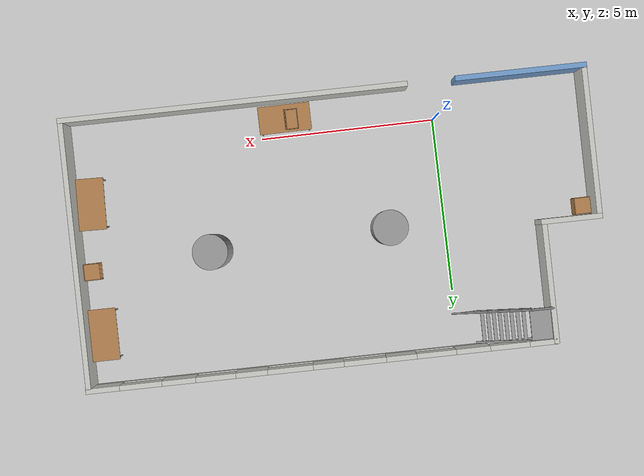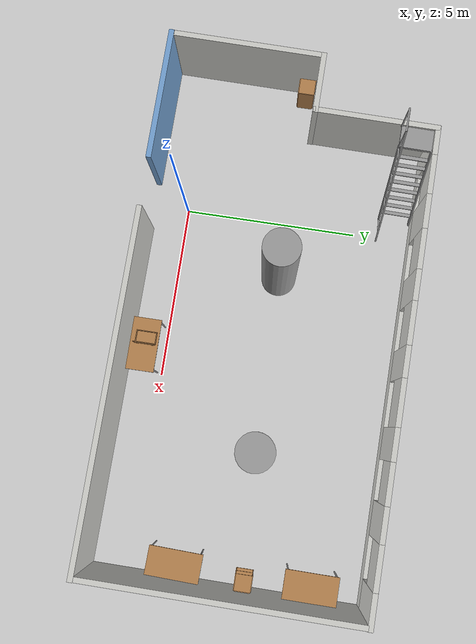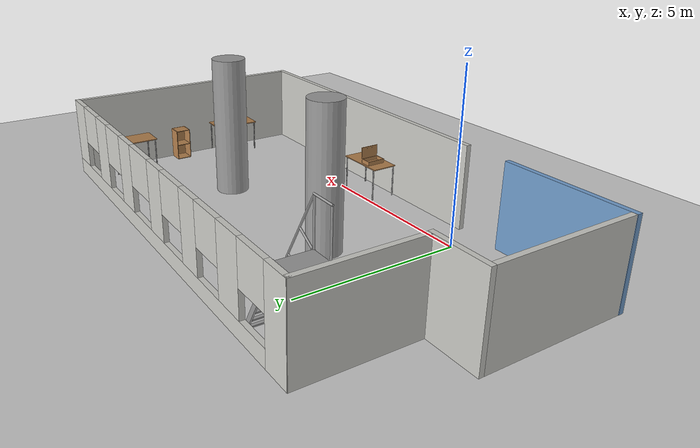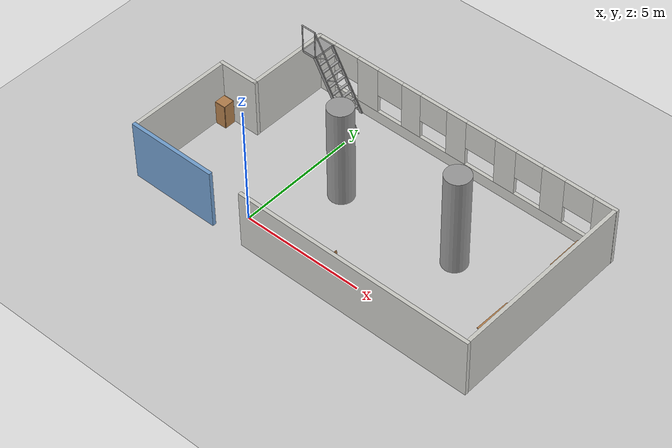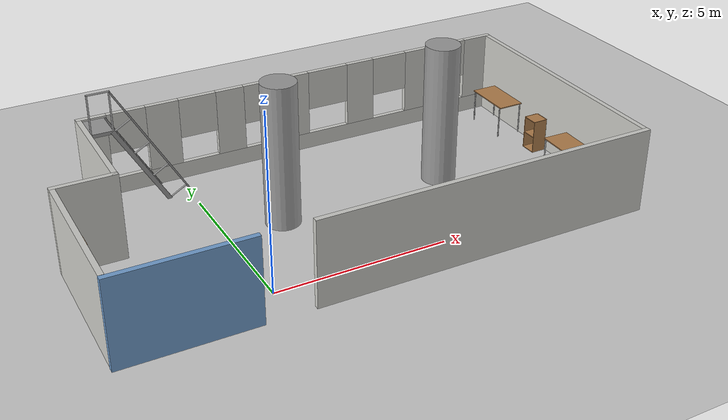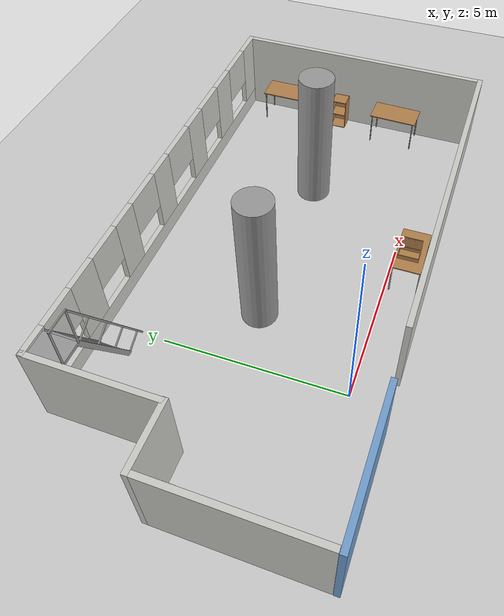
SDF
<sdf version="1.7">
 <world name="default">
  <light name="sun" type="directional">
   <pose>0 0 10 0 -0 0</pose>
   <diffuse>0.8 0.8 0.8 1</diffuse>
   <specular>0.2 0.2 0.2 1</specular>
   <attenuation>
    <range>1000</range>
    <constant>0.9</constant>
    <linear>0.01</linear>
    <quadratic>0.001</quadratic>
   </attenuation>
   <direction>-0.5 0.1 -0.9</direction>
   <spot><inner_angle>0</inner_angle><outer_angle>0</outer_angle><falloff>0</falloff></spot>
  </light>
  <model name="ground_plane">
   <static>1</static>
   <link name="link">
    <collision name="collision">
     <geometry><plane><normal>0 0 1</normal><size>100 100</size></plane></geometry>
     <surface><friction><ode><mu>100</mu><mu2>50</mu2></ode></friction></surface>
    </collision>
    <visual name="visual">
     <cast_shadows>0</cast_shadows>
     <geometry><plane><normal>0 0 1</normal><size>100 100</size></plane></geometry>
     <material>
      <script><uri>file://media/materials/scripts/gazebo.material</uri><name>Gazebo/Grey</name></script>
     </material>
    </visual>
   </link>
  </model>
  <gravity>0 0 -9.8</gravity>
  <magnetic_field>6e-06 2.3e-05 -4.2e-05</magnetic_field>
  <atmosphere type="adiabatic"/>
  <physics type="ode">
   <max_step_size>0.001</max_step_size>
   <real_time_factor>1</real_time_factor>
   <real_time_update_rate>1000</real_time_update_rate>
  </physics>
  <scene><ambient>0.4 0.4 0.4 1</ambient><background>0.7 0.7 0.7 1</background><shadows>1</shadows></scene>
  <spherical_coordinates>
   <surface_model>EARTH_WGS84</surface_model>
   <latitude_deg>0</latitude_deg>
   <longitude_deg>0</longitude_deg>
   <elevation>0</elevation>
   <heading_deg>0</heading_deg>
  </spherical_coordinates>
  <model name="leju_exhibition">
   <link name="Wall_11">
    <pose>-5.68 -2.4925 0 0 -0 0</pose>
    <visual name="Wall_11_Visual">
     <pose>0 0 1.25 0 -0 0</pose>
     <geometry><box><size>3.75 0.15 2.5</size></box></geometry>
     <material>
      <script><uri>file://media/materials/scripts/gazebo.material</uri><name>Gazebo/Grey</name></script>
      <ambient>0.447059 0.623529 0.811765 1</ambient>
      <shader type="pixel"/>
     </material>
     <meta><layer>0</layer></meta>
    </visual>
    <collision name="Wall_11_Collision">
     <pose>0 0 1.25 0 -0 0</pose>
     <geometry><box><size>3.75 0.15 2.5</size></box></geometry>
     <surface>
      <friction>
       <ode><mu>1</mu><mu2>1</mu2><fdir1>0 0 0</fdir1><slip1>0</slip1><slip2>0</slip2></ode>
       <torsional>
        <coefficient>1</coefficient>
        <patch_radius>0</patch_radius>
        <surface_radius>0</surface_radius>
        <use_patch_radius>1</use_patch_radius>
        <ode><slip>0</slip></ode>
       </torsional>
      </friction>
      <bounce><restitution_coefficient>0</restitution_coefficient><threshold>1e+06</threshold></bounce>
      <contact>
       <collide_without_contact>0</collide_without_contact>
       <collide_without_contact_bitmask>1</collide_without_contact_bitmask>
       <collide_bitmask>1</collide_bitmask>
       <ode>
        <soft_cfm>0</soft_cfm>
        <soft_erp>0.2</soft_erp>
        <kp>1e+13</kp>
        <kd>1</kd>
        <max_vel>0.01</max_vel>
        <min_depth>0</min_depth>
       </ode>
       <bullet>
        <split_impulse>1</split_impulse>
        <split_impulse_penetration_threshold>-0.01</split_impulse_penetration_threshold>
        <soft_cfm>0</soft_cfm>
        <soft_erp>0.2</soft_erp>
        <kp>1e+13</kp>
        <kd>1</kd>
       </bullet>
      </contact>
     </surface>
    </collision>
   </link>
   <link name="Wall_13">
    <pose>-7.47239 -0.332597 0 0 -0 1.57079</pose>
    <inertial>
     <inertia><ixx>0</ixx><ixy>0</ixy><ixz>0</ixz><iyy>0</iyy><iyz>0</iyz><izz>0</izz></inertia>
     <mass>0</mass>
    </inertial>
    <visual name="Wall_13_Visual">
     <pose>0 0 1.25 0 -0 0</pose>
     <geometry><box><size>4.15511 0.15 2.5</size></box></geometry>
     <material>
      <script><uri>file://media/materials/scripts/gazebo.material</uri><name>Gazebo/CeilingTiled</name></script>
      <ambient>0.447059 0.623529 0.811765 1</ambient>
      <shader type="pixel"/>
     </material>
     <meta><layer>0</layer></meta>
    </visual>
    <collision name="Wall_13_Collision">
     <pose>0 0 1.25 0 -0 0</pose>
     <geometry><box><size>4.15511 0.15 2.5</size></box></geometry>
     <surface>
      <friction>
       <ode><mu>1</mu><mu2>1</mu2><fdir1>0 0 0</fdir1><slip1>0</slip1><slip2>0</slip2></ode>
       <torsional>
        <coefficient>1</coefficient>
        <patch_radius>0</patch_radius>
        <surface_radius>0</surface_radius>
        <use_patch_radius>1</use_patch_radius>
        <ode><slip>0</slip></ode>
       </torsional>
      </friction>
      <bounce><restitution_coefficient>0</restitution_coefficient><threshold>1e+06</threshold></bounce>
      <contact>
       <collide_without_contact>0</collide_without_contact>
       <collide_without_contact_bitmask>1</collide_without_contact_bitmask>
       <collide_bitmask>1</collide_bitmask>
       <ode>
        <soft_cfm>0</soft_cfm>
        <soft_erp>0.2</soft_erp>
        <kp>1e+13</kp>
        <kd>1</kd>
        <max_vel>0.01</max_vel>
        <min_depth>0</min_depth>
       </ode>
       <bullet>
        <split_impulse>1</split_impulse>
        <split_impulse_penetration_threshold>-0.01</split_impulse_penetration_threshold>
        <soft_cfm>0</soft_cfm>
        <soft_erp>0.2</soft_erp>
        <kp>1e+13</kp>
        <kd>1</kd>
       </bullet>
      </contact>
     </surface>
    </collision>
   </link>
   <link name="Wall_14">
    <pose>-6.67163 1.81563 0 0 -0 0</pose>
    <visual name="Wall_14_Visual">
     <pose>0 0 1.25 0 -0 0</pose>
     <geometry><box><size>1.75 0.15 2.5</size></box></geometry>
     <material>
      <script><uri>file://media/materials/scripts/gazebo.material</uri><name>Gazebo/CeilingTiled</name></script>
      <ambient>0.447059 0.623529 0.811765 1</ambient>
      <shader type="pixel"/>
     </material>
     <meta><layer>0</layer></meta>
    </visual>
    <collision name="Wall_14_Collision">
     <pose>0 0 1.25 0 -0 0</pose>
     <geometry><box><size>1.75 0.15 2.5</size></box></geometry>
     <surface>
      <friction>
       <ode><mu>1</mu><mu2>1</mu2><fdir1>0 0 0</fdir1><slip1>0</slip1><slip2>0</slip2></ode>
       <torsional>
        <coefficient>1</coefficient>
        <patch_radius>0</patch_radius>
        <surface_radius>0</surface_radius>
        <use_patch_radius>1</use_patch_radius>
        <ode><slip>0</slip></ode>
       </torsional>
      </friction>
      <bounce><restitution_coefficient>0</restitution_coefficient><threshold>1e+06</threshold></bounce>
      <contact>
       <collide_without_contact>0</collide_without_contact>
       <collide_without_contact_bitmask>1</collide_without_contact_bitmask>
       <collide_bitmask>1</collide_bitmask>
       <ode>
        <soft_cfm>0</soft_cfm>
        <soft_erp>0.2</soft_erp>
        <kp>1e+13</kp>
        <kd>1</kd>
        <max_vel>0.01</max_vel>
        <min_depth>0</min_depth>
       </ode>
       <bullet>
        <split_impulse>1</split_impulse>
        <split_impulse_penetration_threshold>-0.01</split_impulse_penetration_threshold>
        <soft_cfm>0</soft_cfm>
        <soft_erp>0.2</soft_erp>
        <kp>1e+13</kp>
        <kd>1</kd>
       </bullet>
      </contact>
     </surface>
    </collision>
   </link>
   <link name="Wall_15">
    <pose>-5.8821 3.52008 0 0 -0 1.57079</pose>
    <inertial>
     <inertia><ixx>0</ixx><ixy>0</ixy><ixz>0</ixz><iyy>0</iyy><iyz>0</iyz><izz>0</izz></inertia>
     <mass>0</mass>
    </inertial>
    <visual name="Wall_15_Visual">
     <pose>0 0 1.25 0 -0 0</pose>
     <geometry><box><size>3.54196 0.15 2.5</size></box></geometry>
     <material>
      <script><uri>file://media/materials/scripts/gazebo.material</uri><name>Gazebo/CeilingTiled</name></script>
      <ambient>0.447059 0.623529 0.811765 1</ambient>
      <shader type="pixel"/>
     </material>
     <meta><layer>0</layer></meta>
    </visual>
    <collision name="Wall_15_Collision">
     <pose>0 0 1.25 0 -0 0</pose>
     <geometry><box><size>3.54196 0.15 2.5</size></box></geometry>
     <surface>
      <friction>
       <ode><mu>1</mu><mu2>1</mu2><fdir1>0 0 0</fdir1><slip1>0</slip1><slip2>0</slip2></ode>
       <torsional>
        <coefficient>1</coefficient>
        <patch_radius>0</patch_radius>
        <surface_radius>0</surface_radius>
        <use_patch_radius>1</use_patch_radius>
        <ode><slip>0</slip></ode>
       </torsional>
      </friction>
      <bounce><restitution_coefficient>0</restitution_coefficient><threshold>1e+06</threshold></bounce>
      <contact>
       <collide_without_contact>0</collide_without_contact>
       <collide_without_contact_bitmask>1</collide_without_contact_bitmask>
       <collide_bitmask>1</collide_bitmask>
       <ode>
        <soft_cfm>0</soft_cfm>
        <soft_erp>0.2</soft_erp>
        <kp>1e+13</kp>
        <kd>1</kd>
        <max_vel>0.01</max_vel>
        <min_depth>0</min_depth>
       </ode>
       <bullet>
        <split_impulse>1</split_impulse>
        <split_impulse_penetration_threshold>-0.01</split_impulse_penetration_threshold>
        <soft_cfm>0</soft_cfm>
        <soft_erp>0.2</soft_erp>
        <kp>1e+13</kp>
        <kd>1</kd>
       </bullet>
      </contact>
     </surface>
    </collision>
   </link>
   <link name="Wall_16">
    <pose>0.808087 5.22568 0 0 -0 0</pose>
    <visual name="Wall_16_Visual_0">
     <pose>-6.33395 0 1.25 0 -0 0</pose>
     <geometry><box><size>0.8321 0.15 2.5</size></box></geometry>
     <material>
      <script><uri>file://media/materials/scripts/gazebo.material</uri><name>Gazebo/CeilingTiled</name></script>
      <ambient>0.447059 0.623529 0.811765 1</ambient>
      <shader type="pixel"/>
     </material>
     <meta><layer>0</layer></meta>
    </visual>
    <visual name="Wall_16_Visual_1">
     <pose>0.41605 0 0.25 0 -0 0</pose>
     <geometry><box><size>12.6679 0.15 0.5</size></box></geometry>
     <material>
      <script><uri>file://media/materials/scripts/gazebo.material</uri><name>Gazebo/CeilingTiled</name></script>
      <ambient>0.447059 0.623529 0.811765 1</ambient>
      <shader type="pixel"/>
     </material>
     <meta><layer>0</layer></meta>
    </visual>
    <visual name="Wall_16_Visual_2">
     <pose>-4.31442 0 1.5 0 -0 0</pose>
     <geometry><box><size>0.97215 0.15 2</size></box></geometry>
     <material>
      <script><uri>file://media/materials/scripts/gazebo.material</uri><name>Gazebo/CeilingTiled</name></script>
      <ambient>0.447059 0.623529 0.811765 1</ambient>
      <shader type="pixel"/>
     </material>
     <meta><layer>0</layer></meta>
    </visual>
    <visual name="Wall_16_Visual_3">
     <pose>-2.26455 0 1.5 0 -0 0</pose>
     <geometry><box><size>0.86635 0.15 2</size></box></geometry>
     <material>
      <script><uri>file://media/materials/scripts/gazebo.material</uri><name>Gazebo/CeilingTiled</name></script>
      <ambient>0.447059 0.623529 0.811765 1</ambient>
      <shader type="pixel"/>
     </material>
     <meta><layer>0</layer></meta>
    </visual>
    <visual name="Wall_16_Visual_4">
     <pose>-0.181613 0 1.5 0 -0 0</pose>
     <geometry><box><size>0.879575 0.15 2</size></box></geometry>
     <material>
      <script><uri>file://media/materials/scripts/gazebo.material</uri><name>Gazebo/CeilingTiled</name></script>
      <ambient>0.447059 0.623529 0.811765 1</ambient>
      <shader type="pixel"/>
     </material>
     <meta><layer>0</layer></meta>
    </visual>
    <visual name="Wall_16_Visual_5">
     <pose>2.01374 0 1.5 0 -0 0</pose>
     <geometry><box><size>0.906025 0.15 2</size></box></geometry>
     <material>
      <script><uri>file://media/materials/scripts/gazebo.material</uri><name>Gazebo/CeilingTiled</name></script>
      <ambient>0.447059 0.623529 0.811765 1</ambient>
      <shader type="pixel"/>
     </material>
     <meta><layer>0</layer></meta>
    </visual>
    <visual name="Wall_16_Visual_6">
     <pose>4.09337 0 1.5 0 -0 0</pose>
     <geometry><box><size>0.965538 0.15 2</size></box></geometry>
     <material>
      <script><uri>file://media/materials/scripts/gazebo.material</uri><name>Gazebo/CeilingTiled</name></script>
      <ambient>0.447059 0.623529 0.811765 1</ambient>
      <shader type="pixel"/>
     </material>
     <meta><layer>0</layer></meta>
    </visual>
    <visual name="Wall_16_Visual_7">
     <pose>6.26806 0 1.5 0 -0 0</pose>
     <geometry><box><size>0.963887 0.15 2</size></box></geometry>
     <material>
      <script><uri>file://media/materials/scripts/gazebo.material</uri><name>Gazebo/CeilingTiled</name></script>
      <ambient>0.447059 0.623529 0.811765 1</ambient>
      <shader type="pixel"/>
     </material>
     <meta><layer>0</layer></meta>
    </visual>
    <visual name="Wall_16_Visual_8">
     <pose>-5.3592 0 1.9 0 -0 0</pose>
     <geometry><box><size>1.1174 0.15 1.2</size></box></geometry>
     <material>
      <script><uri>file://media/materials/scripts/gazebo.material</uri><name>Gazebo/CeilingTiled</name></script>
      <ambient>0.447059 0.623529 0.811765 1</ambient>
      <shader type="pixel"/>
     </material>
     <meta><layer>0</layer></meta>
    </visual>
    <visual name="Wall_16_Visual_9">
     <pose>-3.26304 0 1.9 0 -0 0</pose>
     <geometry><box><size>1.13062 0.15 1.2</size></box></geometry>
     <material>
      <script><uri>file://media/materials/scripts/gazebo.material</uri><name>Gazebo/CeilingTiled</name></script>
      <ambient>0.447059 0.623529 0.811765 1</ambient>
      <shader type="pixel"/>
     </material>
     <meta><layer>0</layer></meta>
    </visual>
    <visual name="Wall_16_Visual_10">
     <pose>-1.22639 0 1.9 0 -0 0</pose>
     <geometry><box><size>1.20998 0.15 1.2</size></box></geometry>
     <material>
      <script><uri>file://media/materials/scripts/gazebo.material</uri><name>Gazebo/CeilingTiled</name></script>
      <ambient>0.447059 0.623529 0.811765 1</ambient>
      <shader type="pixel"/>
     </material>
     <meta><layer>0</layer></meta>
    </visual>
    <visual name="Wall_16_Visual_11">
     <pose>0.90945 0 1.9 0 -0 0</pose>
     <geometry><box><size>1.30255 0.15 1.2</size></box></geometry>
     <material>
      <script><uri>file://media/materials/scripts/gazebo.material</uri><name>Gazebo/CeilingTiled</name></script>
      <ambient>0.447059 0.623529 0.811765 1</ambient>
      <shader type="pixel"/>
     </material>
     <meta><layer>0</layer></meta>
    </visual>
    <visual name="Wall_16_Visual_12">
     <pose>3.03868 0 1.9 0 -0 0</pose>
     <geometry><box><size>1.14385 0.15 1.2</size></box></geometry>
     <material>
      <script><uri>file://media/materials/scripts/gazebo.material</uri><name>Gazebo/CeilingTiled</name></script>
      <ambient>0.447059 0.623529 0.811765 1</ambient>
      <shader type="pixel"/>
     </material>
     <meta><layer>0</layer></meta>
    </visual>
    <visual name="Wall_16_Visual_13">
     <pose>5.18112 0 1.9 0 -0 0</pose>
     <geometry><box><size>1.20998 0.15 1.2</size></box></geometry>
     <material>
      <script><uri>file://media/materials/scripts/gazebo.material</uri><name>Gazebo/CeilingTiled</name></script>
      <ambient>0.447059 0.623529 0.811765 1</ambient>
      <shader type="pixel"/>
     </material>
     <meta><layer>0</layer></meta>
    </visual>
    <collision name="Wall_16_Collision_0">
     <pose>-6.33395 0 1.25 0 -0 0</pose>
     <geometry><box><size>0.8321 0.15 2.5</size></box></geometry>
     <surface>
      <friction>
       <ode><mu>1</mu><mu2>1</mu2><fdir1>0 0 0</fdir1><slip1>0</slip1><slip2>0</slip2></ode>
       <torsional>
        <coefficient>1</coefficient>
        <patch_radius>0</patch_radius>
        <surface_radius>0</surface_radius>
        <use_patch_radius>1</use_patch_radius>
        <ode><slip>0</slip></ode>
       </torsional>
      </friction>
      <bounce><restitution_coefficient>0</restitution_coefficient><threshold>1e+06</threshold></bounce>
      <contact>
       <collide_without_contact>0</collide_without_contact>
       <collide_without_contact_bitmask>1</collide_without_contact_bitmask>
       <collide_bitmask>1</collide_bitmask>
       <ode>
        <soft_cfm>0</soft_cfm>
        <soft_erp>0.2</soft_erp>
        <kp>1e+13</kp>
        <kd>1</kd>
        <max_vel>0.01</max_vel>
        <min_depth>0</min_depth>
       </ode>
       <bullet>
        <split_impulse>1</split_impulse>
        <split_impulse_penetration_threshold>-0.01</split_impulse_penetration_threshold>
        <soft_cfm>0</soft_cfm>
        <soft_erp>0.2</soft_erp>
        <kp>1e+13</kp>
        <kd>1</kd>
       </bullet>
      </contact>
     </surface>
    </collision>
    <collision name="Wall_16_Collision_1">
     <pose>0.41605 0 0.25 0 -0 0</pose>
     <geometry><box><size>12.6679 0.15 0.5</size></box></geometry>
     <surface>
      <friction>
       <ode><mu>1</mu><mu2>1</mu2><fdir1>0 0 0</fdir1><slip1>0</slip1><slip2>0</slip2></ode>
       <torsional>
        <coefficient>1</coefficient>
        <patch_radius>0</patch_radius>
        <surface_radius>0</surface_radius>
        <use_patch_radius>1</use_patch_radius>
        <ode><slip>0</slip></ode>
       </torsional>
      </friction>
      <bounce><restitution_coefficient>0</restitution_coefficient><threshold>1e+06</threshold></bounce>
      <contact>
       <collide_without_contact>0</collide_without_contact>
       <collide_without_contact_bitmask>1</collide_without_contact_bitmask>
       <collide_bitmask>1</collide_bitmask>
       <ode>
        <soft_cfm>0</soft_cfm>
        <soft_erp>0.2</soft_erp>
        <kp>1e+13</kp>
        <kd>1</kd>
        <max_vel>0.01</max_vel>
        <min_depth>0</min_depth>
       </ode>
       <bullet>
        <split_impulse>1</split_impulse>
        <split_impulse_penetration_threshold>-0.01</split_impulse_penetration_threshold>
        <soft_cfm>0</soft_cfm>
        <soft_erp>0.2</soft_erp>
        <kp>1e+13</kp>
        <kd>1</kd>
       </bullet>
      </contact>
     </surface>
    </collision>
    <collision name="Wall_16_Collision_2">
     <pose>-4.31442 0 1.5 0 -0 0</pose>
     <geometry><box><size>0.97215 0.15 2</size></box></geometry>
     <surface>
      <friction>
       <ode><mu>1</mu><mu2>1</mu2><fdir1>0 0 0</fdir1><slip1>0</slip1><slip2>0</slip2></ode>
       <torsional>
        <coefficient>1</coefficient>
        <patch_radius>0</patch_radius>
        <surface_radius>0</surface_radius>
        <use_patch_radius>1</use_patch_radius>
        <ode><slip>0</slip></ode>
       </torsional>
      </friction>
      <bounce><restitution_coefficient>0</restitution_coefficient><threshold>1e+06</threshold></bounce>
      <contact>
       <collide_without_contact>0</collide_without_contact>
       <collide_without_contact_bitmask>1</collide_without_contact_bitmask>
       <collide_bitmask>1</collide_bitmask>
       <ode>
        <soft_cfm>0</soft_cfm>
        <soft_erp>0.2</soft_erp>
        <kp>1e+13</kp>
        <kd>1</kd>
        <max_vel>0.01</max_vel>
        <min_depth>0</min_depth>
       </ode>
       <bullet>
        <split_impulse>1</split_impulse>
        <split_impulse_penetration_threshold>-0.01</split_impulse_penetration_threshold>
        <soft_cfm>0</soft_cfm>
        <soft_erp>0.2</soft_erp>
        <kp>1e+13</kp>
        <kd>1</kd>
       </bullet>
      </contact>
     </surface>
    </collision>
    <collision name="Wall_16_Collision_3">
     <pose>-2.26455 0 1.5 0 -0 0</pose>
     <geometry><box><size>0.86635 0.15 2</size></box></geometry>
     <surface>
      <friction>
       <ode><mu>1</mu><mu2>1</mu2><fdir1>0 0 0</fdir1><slip1>0</slip1><slip2>0</slip2></ode>
       <torsional>
        <coefficient>1</coefficient>
        <patch_radius>0</patch_radius>
        <surface_radius>0</surface_radius>
        <use_patch_radius>1</use_patch_radius>
        <ode><slip>0</slip></ode>
       </torsional>
      </friction>
      <bounce><restitution_coefficient>0</restitution_coefficient><threshold>1e+06</threshold></bounce>
      <contact>
       <collide_without_contact>0</collide_without_contact>
       <collide_without_contact_bitmask>1</collide_without_contact_bitmask>
       <collide_bitmask>1</collide_bitmask>
       <ode>
        <soft_cfm>0</soft_cfm>
        <soft_erp>0.2</soft_erp>
        <kp>1e+13</kp>
        <kd>1</kd>
        <max_vel>0.01</max_vel>
        <min_depth>0</min_depth>
       </ode>
       <bullet>
        <split_impulse>1</split_impulse>
        <split_impulse_penetration_threshold>-0.01</split_impulse_penetration_threshold>
        <soft_cfm>0</soft_cfm>
        <soft_erp>0.2</soft_erp>
        <kp>1e+13</kp>
        <kd>1</kd>
       </bullet>
      </contact>
     </surface>
    </collision>
    <collision name="Wall_16_Collision_4">
     <pose>-0.181613 0 1.5 0 -0 0</pose>
     <geometry><box><size>0.879575 0.15 2</size></box></geometry>
     <surface>
      <friction>
       <ode><mu>1</mu><mu2>1</mu2><fdir1>0 0 0</fdir1><slip1>0</slip1><slip2>0</slip2></ode>
       <torsional>
        <coefficient>1</coefficient>
        <patch_radius>0</patch_radius>
        <surface_radius>0</surface_radius>
        <use_patch_radius>1</use_patch_radius>
        <ode><slip>0</slip></ode>
       </torsional>
      </friction>
      <bounce><restitution_coefficient>0</restitution_coefficient><threshold>1e+06</threshold></bounce>
      <contact>
       <collide_without_contact>0</collide_without_contact>
       <collide_without_contact_bitmask>1</collide_without_contact_bitmask>
       <collide_bitmask>1</collide_bitmask>
       <ode>
        <soft_cfm>0</soft_cfm>
        <soft_erp>0.2</soft_erp>
        <kp>1e+13</kp>
        <kd>1</kd>
        <max_vel>0.01</max_vel>
        <min_depth>0</min_depth>
       </ode>
       <bullet>
        <split_impulse>1</split_impulse>
        <split_impulse_penetration_threshold>-0.01</split_impulse_penetration_threshold>
        <soft_cfm>0</soft_cfm>
        <soft_erp>0.2</soft_erp>
        <kp>1e+13</kp>
        <kd>1</kd>
       </bullet>
      </contact>
     </surface>
    </collision>
    <collision name="Wall_16_Collision_5">
     <pose>2.01374 0 1.5 0 -0 0</pose>
     <geometry><box><size>0.906025 0.15 2</size></box></geometry>
     <surface>
      <friction>
       <ode><mu>1</mu><mu2>1</mu2><fdir1>0 0 0</fdir1><slip1>0</slip1><slip2>0</slip2></ode>
       <torsional>
        <coefficient>1</coefficient>
        <patch_radius>0</patch_radius>
        <surface_radius>0</surface_radius>
        <use_patch_radius>1</use_patch_radius>
        <ode><slip>0</slip></ode>
       </torsional>
      </friction>
      <bounce><restitution_coefficient>0</restitution_coefficient><threshold>1e+06</threshold></bounce>
      <contact>
       <collide_without_contact>0</collide_without_contact>
       <collide_without_contact_bitmask>1</collide_without_contact_bitmask>
       <collide_bitmask>1</collide_bitmask>
       <ode>
        <soft_cfm>0</soft_cfm>
        <soft_erp>0.2</soft_erp>
        <kp>1e+13</kp>
        <kd>1</kd>
        <max_vel>0.01</max_vel>
        <min_depth>0</min_depth>
       </ode>
       <bullet>
        <split_impulse>1</split_impulse>
        <split_impulse_penetration_threshold>-0.01</split_impulse_penetration_threshold>
        <soft_cfm>0</soft_cfm>
        <soft_erp>0.2</soft_erp>
        <kp>1e+13</kp>
        <kd>1</kd>
       </bullet>
      </contact>
     </surface>
    </collision>
    <collision name="Wall_16_Collision_6">
     <pose>4.09337 0 1.5 0 -0 0</pose>
     <geometry><box><size>0.965538 0.15 2</size></box></geometry>
     <surface>
      <friction>
       <ode><mu>1</mu><mu2>1</mu2><fdir1>0 0 0</fdir1><slip1>0</slip1><slip2>0</slip2></ode>
       <torsional>
        <coefficient>1</coefficient>
        <patch_radius>0</patch_radius>
        <surface_radius>0</surface_radius>
        <use_patch_radius>1</use_patch_radius>
        <ode><slip>0</slip></ode>
       </torsional>
      </friction>
      <bounce><restitution_coefficient>0</restitution_coefficient><threshold>1e+06</threshold></bounce>
      <contact>
       <collide_without_contact>0</collide_without_contact>
       <collide_without_contact_bitmask>1</collide_without_contact_bitmask>
       <collide_bitmask>1</collide_bitmask>
       <ode>
        <soft_cfm>0</soft_cfm>
        <soft_erp>0.2</soft_erp>
        <kp>1e+13</kp>
        <kd>1</kd>
        <max_vel>0.01</max_vel>
        <min_depth>0</min_depth>
       </ode>
       <bullet>
        <split_impulse>1</split_impulse>
        <split_impulse_penetration_threshold>-0.01</split_impulse_penetration_threshold>
        <soft_cfm>0</soft_cfm>
        <soft_erp>0.2</soft_erp>
        <kp>1e+13</kp>
        <kd>1</kd>
       </bullet>
      </contact>
     </surface>
    </collision>
    <collision name="Wall_16_Collision_7">
     <pose>6.26806 0 1.5 0 -0 0</pose>
     <geometry><box><size>0.963887 0.15 2</size></box></geometry>
     <surface>
      <friction>
       <ode><mu>1</mu><mu2>1</mu2><fdir1>0 0 0</fdir1><slip1>0</slip1><slip2>0</slip2></ode>
       <torsional>
        <coefficient>1</coefficient>
        <patch_radius>0</patch_radius>
        <surface_radius>0</surface_radius>
        <use_patch_radius>1</use_patch_radius>
        <ode><slip>0</slip></ode>
       </torsional>
      </friction>
      <bounce><restitution_coefficient>0</restitution_coefficient><threshold>1e+06</threshold></bounce>
      <contact>
       <collide_without_contact>0</collide_without_contact>
       <collide_without_contact_bitmask>1</collide_without_contact_bitmask>
       <collide_bitmask>1</collide_bitmask>
       <ode>
        <soft_cfm>0</soft_cfm>
        <soft_erp>0.2</soft_erp>
        <kp>1e+13</kp>
        <kd>1</kd>
        <max_vel>0.01</max_vel>
        <min_depth>0</min_depth>
       </ode>
       <bullet>
        <split_impulse>1</split_impulse>
        <split_impulse_penetration_threshold>-0.01</split_impulse_penetration_threshold>
        <soft_cfm>0</soft_cfm>
        <soft_erp>0.2</soft_erp>
        <kp>1e+13</kp>
        <kd>1</kd>
       </bullet>
      </contact>
     </surface>
    </collision>
    <collision name="Wall_16_Collision_8">
     <pose>-5.3592 0 1.9 0 -0 0</pose>
     <geometry><box><size>1.1174 0.15 1.2</size></box></geometry>
     <surface>
      <friction>
       <ode><mu>1</mu><mu2>1</mu2><fdir1>0 0 0</fdir1><slip1>0</slip1><slip2>0</slip2></ode>
       <torsional>
        <coefficient>1</coefficient>
        <patch_radius>0</patch_radius>
        <surface_radius>0</surface_radius>
        <use_patch_radius>1</use_patch_radius>
        <ode><slip>0</slip></ode>
       </torsional>
      </friction>
      <bounce><restitution_coefficient>0</restitution_coefficient><threshold>1e+06</threshold></bounce>
      <contact>
       <collide_without_contact>0</collide_without_contact>
       <collide_without_contact_bitmask>1</collide_without_contact_bitmask>
       <collide_bitmask>1</collide_bitmask>
       <ode>
        <soft_cfm>0</soft_cfm>
        <soft_erp>0.2</soft_erp>
        <kp>1e+13</kp>
        <kd>1</kd>
        <max_vel>0.01</max_vel>
        <min_depth>0</min_depth>
       </ode>
       <bullet>
        <split_impulse>1</split_impulse>
        <split_impulse_penetration_threshold>-0.01</split_impulse_penetration_threshold>
        <soft_cfm>0</soft_cfm>
        <soft_erp>0.2</soft_erp>
        <kp>1e+13</kp>
        <kd>1</kd>
       </bullet>
      </contact>
     </surface>
    </collision>
    <collision name="Wall_16_Collision_9">
     <pose>-3.26304 0 1.9 0 -0 0</pose>
     <geometry><box><size>1.13062 0.15 1.2</size></box></geometry>
     <surface>
      <friction>
       <ode><mu>1</mu><mu2>1</mu2><fdir1>0 0 0</fdir1><slip1>0</slip1><slip2>0</slip2></ode>
       <torsional>
        <coefficient>1</coefficient>
        <patch_radius>0</patch_radius>
        <surface_radius>0</surface_radius>
        <use_patch_radius>1</use_patch_radius>
        <ode><slip>0</slip></ode>
       </torsional>
      </friction>
      <bounce><restitution_coefficient>0</restitution_coefficient><threshold>1e+06</threshold></bounce>
      <contact>
       <collide_without_contact>0</collide_without_contact>
       <collide_without_contact_bitmask>1</collide_without_contact_bitmask>
       <collide_bitmask>1</collide_bitmask>
       <ode>
        <soft_cfm>0</soft_cfm>
        <soft_erp>0.2</soft_erp>
        <kp>1e+13</kp>
        <kd>1</kd>
        <max_vel>0.01</max_vel>
        <min_depth>0</min_depth>
       </ode>
       <bullet>
        <split_impulse>1</split_impulse>
        <split_impulse_penetration_threshold>-0.01</split_impulse_penetration_threshold>
        <soft_cfm>0</soft_cfm>
        <soft_erp>0.2</soft_erp>
        <kp>1e+13</kp>
        <kd>1</kd>
       </bullet>
      </contact>
     </surface>
    </collision>
    <collision name="Wall_16_Collision_10">
     <pose>-1.22639 0 1.9 0 -0 0</pose>
     <geometry><box><size>1.20998 0.15 1.2</size></box></geometry>
     <surface>
      <friction>
       <ode><mu>1</mu><mu2>1</mu2><fdir1>0 0 0</fdir1><slip1>0</slip1><slip2>0</slip2></ode>
       <torsional>
        <coefficient>1</coefficient>
        <patch_radius>0</patch_radius>
        <surface_radius>0</surface_radius>
        <use_patch_radius>1</use_patch_radius>
        <ode><slip>0</slip></ode>
       </torsional>
      </friction>
      <bounce><restitution_coefficient>0</restitution_coefficient><threshold>1e+06</threshold></bounce>
      <contact>
       <collide_without_contact>0</collide_without_contact>
       <collide_without_contact_bitmask>1</collide_without_contact_bitmask>
       <collide_bitmask>1</collide_bitmask>
       <ode>
        <soft_cfm>0</soft_cfm>
        <soft_erp>0.2</soft_erp>
        <kp>1e+13</kp>
        <kd>1</kd>
        <max_vel>0.01</max_vel>
        <min_depth>0</min_depth>
       </ode>
       <bullet>
        <split_impulse>1</split_impulse>
        <split_impulse_penetration_threshold>-0.01</split_impulse_penetration_threshold>
        <soft_cfm>0</soft_cfm>
        <soft_erp>0.2</soft_erp>
        <kp>1e+13</kp>
        <kd>1</kd>
       </bullet>
      </contact>
     </surface>
    </collision>
    <collision name="Wall_16_Collision_11">
     <pose>0.90945 0 1.9 0 -0 0</pose>
     <geometry><box><size>1.30255 0.15 1.2</size></box></geometry>
     <surface>
      <friction>
       <ode><mu>1</mu><mu2>1</mu2><fdir1>0 0 0</fdir1><slip1>0</slip1><slip2>0</slip2></ode>
       <torsional>
        <coefficient>1</coefficient>
        <patch_radius>0</patch_radius>
        <surface_radius>0</surface_radius>
        <use_patch_radius>1</use_patch_radius>
        <ode><slip>0</slip></ode>
       </torsional>
      </friction>
      <bounce><restitution_coefficient>0</restitution_coefficient><threshold>1e+06</threshold></bounce>
      <contact>
       <collide_without_contact>0</collide_without_contact>
       <collide_without_contact_bitmask>1</collide_without_contact_bitmask>
       <collide_bitmask>1</collide_bitmask>
       <ode>
        <soft_cfm>0</soft_cfm>
        <soft_erp>0.2</soft_erp>
        <kp>1e+13</kp>
        <kd>1</kd>
        <max_vel>0.01</max_vel>
        <min_depth>0</min_depth>
       </ode>
       <bullet>
        <split_impulse>1</split_impulse>
        <split_impulse_penetration_threshold>-0.01</split_impulse_penetration_threshold>
        <soft_cfm>0</soft_cfm>
        <soft_erp>0.2</soft_erp>
        <kp>1e+13</kp>
        <kd>1</kd>
       </bullet>
      </contact>
     </surface>
    </collision>
    <collision name="Wall_16_Collision_12">
     <pose>3.03868 0 1.9 0 -0 0</pose>
     <geometry><box><size>1.14385 0.15 1.2</size></box></geometry>
     <surface>
      <friction>
       <ode><mu>1</mu><mu2>1</mu2><fdir1>0 0 0</fdir1><slip1>0</slip1><slip2>0</slip2></ode>
       <torsional>
        <coefficient>1</coefficient>
        <patch_radius>0</patch_radius>
        <surface_radius>0</surface_radius>
        <use_patch_radius>1</use_patch_radius>
        <ode><slip>0</slip></ode>
       </torsional>
      </friction>
      <bounce><restitution_coefficient>0</restitution_coefficient><threshold>1e+06</threshold></bounce>
      <contact>
       <collide_without_contact>0</collide_without_contact>
       <collide_without_contact_bitmask>1</collide_without_contact_bitmask>
       <collide_bitmask>1</collide_bitmask>
       <ode>
        <soft_cfm>0</soft_cfm>
        <soft_erp>0.2</soft_erp>
        <kp>1e+13</kp>
        <kd>1</kd>
        <max_vel>0.01</max_vel>
        <min_depth>0</min_depth>
       </ode>
       <bullet>
        <split_impulse>1</split_impulse>
        <split_impulse_penetration_threshold>-0.01</split_impulse_penetration_threshold>
        <soft_cfm>0</soft_cfm>
        <soft_erp>0.2</soft_erp>
        <kp>1e+13</kp>
        <kd>1</kd>
       </bullet>
      </contact>
     </surface>
    </collision>
    <collision name="Wall_16_Collision_13">
     <pose>5.18112 0 1.9 0 -0 0</pose>
     <geometry><box><size>1.20998 0.15 1.2</size></box></geometry>
     <surface>
      <friction>
       <ode><mu>1</mu><mu2>1</mu2><fdir1>0 0 0</fdir1><slip1>0</slip1><slip2>0</slip2></ode>
       <torsional>
        <coefficient>1</coefficient>
        <patch_radius>0</patch_radius>
        <surface_radius>0</surface_radius>
        <use_patch_radius>1</use_patch_radius>
        <ode><slip>0</slip></ode>
       </torsional>
      </friction>
      <bounce><restitution_coefficient>0</restitution_coefficient><threshold>1e+06</threshold></bounce>
      <contact>
       <collide_without_contact>0</collide_without_contact>
       <collide_without_contact_bitmask>1</collide_without_contact_bitmask>
       <collide_bitmask>1</collide_bitmask>
       <ode>
        <soft_cfm>0</soft_cfm>
        <soft_erp>0.2</soft_erp>
        <kp>1e+13</kp>
        <kd>1</kd>
        <max_vel>0.01</max_vel>
        <min_depth>0</min_depth>
       </ode>
       <bullet>
        <split_impulse>1</split_impulse>
        <split_impulse_penetration_threshold>-0.01</split_impulse_penetration_threshold>
        <soft_cfm>0</soft_cfm>
        <soft_erp>0.2</soft_erp>
        <kp>1e+13</kp>
        <kd>1</kd>
       </bullet>
      </contact>
     </surface>
    </collision>
   </link>
   <link name="Wall_17">
    <pose>7.47238 1.38023 0 0 0 -1.5708</pose>
    <inertial>
     <inertia><ixx>0</ixx><ixy>0</ixy><ixz>0</ixz><iyy>0</iyy><iyz>0</iyz><izz>0</izz></inertia>
     <mass>0</mass>
    </inertial>
    <visual name="Wall_17_Visual">
     <pose>0 0 1.25 0 -0 0</pose>
     <geometry><box><size>7.59323 0.15 2.5</size></box></geometry>
     <material>
      <script><uri>file://media/materials/scripts/gazebo.material</uri><name>Gazebo/CeilingTiled</name></script>
      <ambient>0.447059 0.623529 0.811765 1</ambient>
      <shader type="pixel"/>
     </material>
     <meta><layer>0</layer></meta>
    </visual>
    <collision name="Wall_17_Collision">
     <pose>0 0 1.25 0 -0 0</pose>
     <geometry><box><size>7.59323 0.15 2.5</size></box></geometry>
     <surface>
      <friction>
       <ode><mu>1</mu><mu2>1</mu2><fdir1>0 0 0</fdir1><slip1>0</slip1><slip2>0</slip2></ode>
       <torsional>
        <coefficient>1</coefficient>
        <patch_radius>0</patch_radius>
        <surface_radius>0</surface_radius>
        <use_patch_radius>1</use_patch_radius>
        <ode><slip>0</slip></ode>
       </torsional>
      </friction>
      <bounce><restitution_coefficient>0</restitution_coefficient><threshold>1e+06</threshold></bounce>
      <contact>
       <collide_without_contact>0</collide_without_contact>
       <collide_without_contact_bitmask>1</collide_without_contact_bitmask>
       <collide_bitmask>1</collide_bitmask>
       <ode>
        <soft_cfm>0</soft_cfm>
        <soft_erp>0.2</soft_erp>
        <kp>1e+13</kp>
        <kd>1</kd>
        <max_vel>0.01</max_vel>
        <min_depth>0</min_depth>
       </ode>
       <bullet>
        <split_impulse>1</split_impulse>
        <split_impulse_penetration_threshold>-0.01</split_impulse_penetration_threshold>
        <soft_cfm>0</soft_cfm>
        <soft_erp>0.2</soft_erp>
        <kp>1e+13</kp>
        <kd>1</kd>
       </bullet>
      </contact>
     </surface>
    </collision>
   </link>
   <link name="Wall_18">
    <pose>2.555 -2.4925 0 0 -0 3.14159</pose>
    <visual name="Wall_18_Visual">
     <pose>0 0 1.25 0 -0 0</pose>
     <geometry><box><size>10 0.15 2.5</size></box></geometry>
     <material>
      <script><uri>file://media/materials/scripts/gazebo.material</uri><name>Gazebo/CeilingTiled</name></script>
      <ambient>0.447059 0.623529 0.811765 1</ambient>
      <shader type="pixel"/>
     </material>
     <meta><layer>0</layer></meta>
    </visual>
    <collision name="Wall_18_Collision">
     <pose>0 0 1.25 0 -0 0</pose>
     <geometry><box><size>10 0.15 2.5</size></box></geometry>
     <surface>
      <friction>
       <ode><mu>1</mu><mu2>1</mu2><fdir1>0 0 0</fdir1><slip1>0</slip1><slip2>0</slip2></ode>
       <torsional>
        <coefficient>1</coefficient>
        <patch_radius>0</patch_radius>
        <surface_radius>0</surface_radius>
        <use_patch_radius>1</use_patch_radius>
        <ode><slip>0</slip></ode>
       </torsional>
      </friction>
      <bounce><restitution_coefficient>0</restitution_coefficient><threshold>1e+06</threshold></bounce>
      <contact>
       <collide_without_contact>0</collide_without_contact>
       <collide_without_contact_bitmask>1</collide_without_contact_bitmask>
       <collide_bitmask>1</collide_bitmask>
       <ode>
        <soft_cfm>0</soft_cfm>
        <soft_erp>0.2</soft_erp>
        <kp>1e+13</kp>
        <kd>1</kd>
        <max_vel>0.01</max_vel>
        <min_depth>0</min_depth>
       </ode>
       <bullet>
        <split_impulse>1</split_impulse>
        <split_impulse_penetration_threshold>-0.01</split_impulse_penetration_threshold>
        <soft_cfm>0</soft_cfm>
        <soft_erp>0.2</soft_erp>
        <kp>1e+13</kp>
        <kd>1</kd>
       </bullet>
      </contact>
     </surface>
    </collision>
   </link>
   <static>1</static>
   <pose>3.14518 1.44437 -0.00345 0 0 -0.008372</pose>
  </model>
  <model name="unit_cylinder_clone">
   <pose>6.71281 3.07456 2.10043 0 -0 -8.1e-05</pose>
   <link name="link">
    <inertial>
     <mass>1</mass>
     <inertia><ixx>0.145833</ixx><ixy>0</ixy><ixz>0</ixz><iyy>0.145833</iyy><iyz>0</iyz><izz>0.125</izz></inertia>
    </inertial>
    <collision name="collision">
     <geometry><cylinder><radius>0.5</radius><length>4.20087</length></cylinder></geometry>
    </collision>
    <visual name="visual">
     <geometry><cylinder><radius>0.5</radius><length>4.20087</length></cylinder></geometry>
     <material>
      <script><name>Gazebo/Grey</name><uri>file://media/materials/scripts/gazebo.material</uri></script>
     </material>
    </visual>
   </link>
  </model>
  <model name="table">
   <static>1</static>
   <link name="link">
    <collision name="surface">
     <pose>0 0 1 0 -0 0</pose>
     <geometry><box><size>1.5 0.8 0.03</size></box></geometry>
     <surface><friction><ode><mu>0.6</mu><mu2>0.6</mu2></ode></friction></surface>
    </collision>
    <visual name="visual1">
     <pose>0 0 1 0 -0 0</pose>
     <geometry><box><size>1.5 0.8 0.03</size></box></geometry>
     <material>
      <script><uri>file://media/materials/scripts/gazebo.material</uri><name>Gazebo/Wood</name></script>
     </material>
    </visual>
    <collision name="front_left_leg">
     <pose>0.68 0.38 0.5 0 -0 0</pose>
     <geometry><cylinder><radius>0.02</radius><length>1</length></cylinder></geometry>
    </collision>
    <visual name="front_left_leg">
     <pose>0.68 0.38 0.5 0 -0 0</pose>
     <geometry><cylinder><radius>0.02</radius><length>1</length></cylinder></geometry>
     <material>
      <script><uri>file://media/materials/scripts/gazebo.material</uri><name>Gazebo/Grey</name></script>
     </material>
    </visual>
    <collision name="front_right_leg">
     <pose>0.68 -0.38 0.5 0 -0 0</pose>
     <geometry><cylinder><radius>0.02</radius><length>1</length></cylinder></geometry>
    </collision>
    <visual name="front_right_leg">
     <pose>0.68 -0.38 0.5 0 -0 0</pose>
     <geometry><cylinder><radius>0.02</radius><length>1</length></cylinder></geometry>
     <material>
      <script><uri>file://media/materials/scripts/gazebo.material</uri><name>Gazebo/Grey</name></script>
     </material>
    </visual>
    <collision name="back_right_leg">
     <pose>-0.68 -0.38 0.5 0 -0 0</pose>
     <geometry><cylinder><radius>0.02</radius><length>1</length></cylinder></geometry>
    </collision>
    <visual name="back_right_leg">
     <pose>-0.68 -0.38 0.5 0 -0 0</pose>
     <geometry><cylinder><radius>0.02</radius><length>1</length></cylinder></geometry>
     <material>
      <script><uri>file://media/materials/scripts/gazebo.material</uri><name>Gazebo/Grey</name></script>
     </material>
    </visual>
    <collision name="back_left_leg">
     <pose>-0.68 0.38 0.5 0 -0 0</pose>
     <geometry><cylinder><radius>0.02</radius><length>1</length></cylinder></geometry>
    </collision>
    <visual name="back_left_leg">
     <pose>-0.68 0.38 0.5 0 -0 0</pose>
     <geometry><cylinder><radius>0.02</radius><length>1</length></cylinder></geometry>
     <material>
      <script><uri>file://media/materials/scripts/gazebo.material</uri><name>Gazebo/Grey</name></script>
     </material>
    </visual>
   </link>
   <pose>10.1652 5.10126 0 0 0 -1.57912</pose>
  </model>
  <model name="cabinet">
   <static>1</static>
   <link name="cabinet_bottom_plate">
    <inertial>
     <pose>0 0 -1 0 -0 0</pose>
     <inertia><ixx>2.05</ixx><ixy>0</ixy><ixz>0</ixz><iyy>2.05</iyy><iyz>0</iyz><izz>2.05</izz></inertia>
     <mass>25</mass>
    </inertial>
    <collision name="cabinet_bottom_plate_geom">
     <pose>0 0 0.01 0 -0 0</pose>
     <geometry><box><size>0.45 0.45 0.02</size></box></geometry>
    </collision>
    <visual name="cabinet_bottom_plate_geom_visual">
     <pose>0 0 0.01 0 -0 0</pose>
     <geometry><box><size>0.45 0.45 0.02</size></box></geometry>
     <material>
      <script><uri>file://media/materials/scripts/gazebo.material</uri><name>Gazebo/Wood</name></script>
     </material>
    </visual>
    <collision name="cabinet_bottom_plate_geom_cabinet_back_plate">
     <pose>0.235 0 0.51 0 -0 0</pose>
     <geometry><box><size>0.02 0.45 1.02</size></box></geometry>
    </collision>
    <visual name="cabinet_bottom_plate_geom_cabinet_back_plate_visual">
     <pose>0.235 0 0.51 0 -0 0</pose>
     <geometry><box><size>0.02 0.45 1.02</size></box></geometry>
     <material>
      <script><uri>file://media/materials/scripts/gazebo.material</uri><name>Gazebo/Wood</name></script>
     </material>
    </visual>
    <collision name="cabinet_bottom_plate_geom_cabinet_left_plate">
     <pose>0 0.235 0.51 0 -0 0</pose>
     <geometry><box><size>0.45 0.02 1.02</size></box></geometry>
    </collision>
    <visual name="cabinet_bottom_plate_geom_cabinet_left_plate_visual">
     <pose>0 0.235 0.51 0 -0 0</pose>
     <geometry><box><size>0.45 0.02 1.02</size></box></geometry>
     <material>
      <script><uri>file://media/materials/scripts/gazebo.material</uri><name>Gazebo/Wood</name></script>
     </material>
    </visual>
    <collision name="cabinet_bottom_plate_geom_cabinet_middle_plate">
     <pose>0 0 0.51 0 -0 0</pose>
     <geometry><box><size>0.45 0.45 0.02</size></box></geometry>
    </collision>
    <visual name="cabinet_bottom_plate_geom_cabinet_middle_plate_visual">
     <pose>0 0 0.51 0 -0 0</pose>
     <geometry><box><size>0.45 0.45 0.02</size></box></geometry>
     <material>
      <script><uri>file://media/materials/scripts/gazebo.material</uri><name>Gazebo/Wood</name></script>
     </material>
    </visual>
    <collision name="cabinet_bottom_plate_geom_cabinet_right_plate">
     <pose>0 -0.235 0.51 0 -0 0</pose>
     <geometry><box><size>0.45 0.02 1.02</size></box></geometry>
    </collision>
    <visual name="cabinet_bottom_plate_geom_cabinet_right_plate_visual">
     <pose>0 -0.235 0.51 0 -0 0</pose>
     <geometry><box><size>0.45 0.02 1.02</size></box></geometry>
     <material>
      <script><uri>file://media/materials/scripts/gazebo.material</uri><name>Gazebo/Wood</name></script>
     </material>
    </visual>
    <collision name="cabinet_bottom_plate_geom_cabinet_top_plate">
     <pose>0 0 1.01 0 -0 0</pose>
     <geometry><box><size>0.45 0.45 0.02</size></box></geometry>
    </collision>
    <visual name="cabinet_bottom_plate_geom_cabinet_top_plate_visual">
     <pose>0 0 1.01 0 -0 0</pose>
     <geometry><box><size>0.45 0.45 0.02</size></box></geometry>
     <material>
      <script><uri>file://media/materials/scripts/gazebo.material</uri><name>Gazebo/Wood</name></script>
     </material>
    </visual>
   </link>
   <pose>-3.99396 2.98248 0 0 -0 0</pose>
  </model>
  <model name="table_0">
   <static>1</static>
   <link name="link">
    <collision name="surface">
     <pose>0 0 1 0 -0 0</pose>
     <geometry><box><size>1.5 0.8 0.03</size></box></geometry>
     <surface><friction><ode><mu>0.6</mu><mu2>0.6</mu2></ode></friction></surface>
    </collision>
    <visual name="visual1">
     <pose>0 0 1 0 -0 0</pose>
     <geometry><box><size>1.5 0.8 0.03</size></box></geometry>
     <material>
      <script><uri>file://media/materials/scripts/gazebo.material</uri><name>Gazebo/Wood</name></script>
     </material>
    </visual>
    <collision name="front_left_leg">
     <pose>0.68 0.38 0.5 0 -0 0</pose>
     <geometry><cylinder><radius>0.02</radius><length>1</length></cylinder></geometry>
    </collision>
    <visual name="front_left_leg">
     <pose>0.68 0.38 0.5 0 -0 0</pose>
     <geometry><cylinder><radius>0.02</radius><length>1</length></cylinder></geometry>
     <material>
      <script><uri>file://media/materials/scripts/gazebo.material</uri><name>Gazebo/Grey</name></script>
     </material>
    </visual>
    <collision name="front_right_leg">
     <pose>0.68 -0.38 0.5 0 -0 0</pose>
     <geometry><cylinder><radius>0.02</radius><length>1</length></cylinder></geometry>
    </collision>
    <visual name="front_right_leg">
     <pose>0.68 -0.38 0.5 0 -0 0</pose>
     <geometry><cylinder><radius>0.02</radius><length>1</length></cylinder></geometry>
     <material>
      <script><uri>file://media/materials/scripts/gazebo.material</uri><name>Gazebo/Grey</name></script>
     </material>
    </visual>
    <collision name="back_right_leg">
     <pose>-0.68 -0.38 0.5 0 -0 0</pose>
     <geometry><cylinder><radius>0.02</radius><length>1</length></cylinder></geometry>
    </collision>
    <visual name="back_right_leg">
     <pose>-0.68 -0.38 0.5 0 -0 0</pose>
     <geometry><cylinder><radius>0.02</radius><length>1</length></cylinder></geometry>
     <material>
      <script><uri>file://media/materials/scripts/gazebo.material</uri><name>Gazebo/Grey</name></script>
     </material>
    </visual>
    <collision name="back_left_leg">
     <pose>-0.68 0.38 0.5 0 -0 0</pose>
     <geometry><cylinder><radius>0.02</radius><length>1</length></cylinder></geometry>
    </collision>
    <visual name="back_left_leg">
     <pose>-0.68 0.38 0.5 0 -0 0</pose>
     <geometry><cylinder><radius>0.02</radius><length>1</length></cylinder></geometry>
     <material>
      <script><uri>file://media/materials/scripts/gazebo.material</uri><name>Gazebo/Grey</name></script>
     </material>
    </visual>
   </link>
   <pose>10.1047 1.31611 0 0 -0 1.53814</pose>
  </model>
  <model name="cabinet_0">
   <static>1</static>
   <link name="cabinet_bottom_plate">
    <inertial>
     <pose>0 0 -1 0 -0 0</pose>
     <inertia><ixx>2.05</ixx><ixy>0</ixy><ixz>0</ixz><iyy>2.05</iyy><iyz>0</iyz><izz>2.05</izz></inertia>
     <mass>25</mass>
    </inertial>
    <collision name="cabinet_bottom_plate_geom">
     <pose>0 0 0.01 0 -0 0</pose>
     <geometry><box><size>0.45 0.45 0.02</size></box></geometry>
    </collision>
    <visual name="cabinet_bottom_plate_geom_visual">
     <pose>0 0 0.01 0 -0 0</pose>
     <geometry><box><size>0.45 0.45 0.02</size></box></geometry>
     <material>
      <script><uri>file://media/materials/scripts/gazebo.material</uri><name>Gazebo/Wood</name></script>
     </material>
    </visual>
    <collision name="cabinet_bottom_plate_geom_cabinet_back_plate">
     <pose>0.235 0 0.51 0 -0 0</pose>
     <geometry><box><size>0.02 0.45 1.02</size></box></geometry>
    </collision>
    <visual name="cabinet_bottom_plate_geom_cabinet_back_plate_visual">
     <pose>0.235 0 0.51 0 -0 0</pose>
     <geometry><box><size>0.02 0.45 1.02</size></box></geometry>
     <material>
      <script><uri>file://media/materials/scripts/gazebo.material</uri><name>Gazebo/Wood</name></script>
     </material>
    </visual>
    <collision name="cabinet_bottom_plate_geom_cabinet_left_plate">
     <pose>0 0.235 0.51 0 -0 0</pose>
     <geometry><box><size>0.45 0.02 1.02</size></box></geometry>
    </collision>
    <visual name="cabinet_bottom_plate_geom_cabinet_left_plate_visual">
     <pose>0 0.235 0.51 0 -0 0</pose>
     <geometry><box><size>0.45 0.02 1.02</size></box></geometry>
     <material>
      <script><uri>file://media/materials/scripts/gazebo.material</uri><name>Gazebo/Wood</name></script>
     </material>
    </visual>
    <collision name="cabinet_bottom_plate_geom_cabinet_middle_plate">
     <pose>0 0 0.51 0 -0 0</pose>
     <geometry><box><size>0.45 0.45 0.02</size></box></geometry>
    </collision>
    <visual name="cabinet_bottom_plate_geom_cabinet_middle_plate_visual">
     <pose>0 0 0.51 0 -0 0</pose>
     <geometry><box><size>0.45 0.45 0.02</size></box></geometry>
     <material>
      <script><uri>file://media/materials/scripts/gazebo.material</uri><name>Gazebo/Wood</name></script>
     </material>
    </visual>
    <collision name="cabinet_bottom_plate_geom_cabinet_right_plate">
     <pose>0 -0.235 0.51 0 -0 0</pose>
     <geometry><box><size>0.45 0.02 1.02</size></box></geometry>
    </collision>
    <visual name="cabinet_bottom_plate_geom_cabinet_right_plate_visual">
     <pose>0 -0.235 0.51 0 -0 0</pose>
     <geometry><box><size>0.45 0.02 1.02</size></box></geometry>
     <material>
      <script><uri>file://media/materials/scripts/gazebo.material</uri><name>Gazebo/Wood</name></script>
     </material>
    </visual>
    <collision name="cabinet_bottom_plate_geom_cabinet_top_plate">
     <pose>0 0 1.01 0 -0 0</pose>
     <geometry><box><size>0.45 0.45 0.02</size></box></geometry>
    </collision>
    <visual name="cabinet_bottom_plate_geom_cabinet_top_plate_visual">
     <pose>0 0 1.01 0 -0 0</pose>
     <geometry><box><size>0.45 0.45 0.02</size></box></geometry>
     <material>
      <script><uri>file://media/materials/scripts/gazebo.material</uri><name>Gazebo/Wood</name></script>
     </material>
    </visual>
   </link>
   <pose>10.3055 3.26064 0 0 -0 0</pose>
  </model>
  <model name="unit_cylinder_clone_clone">
   <pose>1.65852 2.97493 2.10043 0 -0 -0.000642</pose>
   <link name="link">
    <inertial>
     <mass>1</mass>
     <inertia><ixx>0.145833</ixx><ixy>0</ixy><ixz>0</ixz><iyy>0.145833</iyy><iyz>0</iyz><izz>0.125</izz></inertia>
    </inertial>
    <collision name="collision">
     <geometry><cylinder><radius>0.5</radius><length>4.20087</length></cylinder></geometry>
    </collision>
    <visual name="visual">
     <geometry><cylinder><radius>0.5</radius><length>4.20087</length></cylinder></geometry>
     <material>
      <script><name>Gazebo/Grey</name><uri>file://media/materials/scripts/gazebo.material</uri></script>
     </material>
    </visual>
   </link>
  </model>
  <model name="ladder_60deg_1rails">
   <static>1</static>
   <link name="step0">
    <pose>0 0.15396 0.266667 0 -0 0</pose>
    <inertial>
     <mass>9.75482</mass>
     <inertia>
      <ixx>0.00957124</ixx>
      <iyy>0.65963</iyy>
      <izz>0.666842</izz>
      <ixy>0</ixy>
      <ixz>0</ixz>
      <iyz>0</iyz>
     </inertia>
    </inertial>
    <collision name="collision"><geometry><box><size>0.9 0.1016 0.0381</size></box></geometry></collision>
    <visual name="visual">
     <geometry><box><size>0.9 0.1016 0.0381</size></box></geometry>
     <material>
      <script><uri>file://media/materials/scripts/gazebo.material</uri><name>Gazebo/Grey</name></script>
     </material>
    </visual>
   </link>
   <link name="step1">
    <pose>0 0.30792 0.533333 0 -0 0</pose>
    <inertial>
     <mass>9.75482</mass>
     <inertia>
      <ixx>0.00957124</ixx>
      <iyy>0.65963</iyy>
      <izz>0.666842</izz>
      <ixy>0</ixy>
      <ixz>0</ixz>
      <iyz>0</iyz>
     </inertia>
    </inertial>
    <collision name="collision"><geometry><box><size>0.9 0.1016 0.0381</size></box></geometry></collision>
    <visual name="visual">
     <geometry><box><size>0.9 0.1016 0.0381</size></box></geometry>
     <material>
      <script><uri>file://media/materials/scripts/gazebo.material</uri><name>Gazebo/Grey</name></script>
     </material>
    </visual>
   </link>
   <link name="step2">
    <pose>0 0.46188 0.8 0 -0 0</pose>
    <inertial>
     <mass>9.75482</mass>
     <inertia>
      <ixx>0.00957124</ixx>
      <iyy>0.65963</iyy>
      <izz>0.666842</izz>
      <ixy>0</ixy>
      <ixz>0</ixz>
      <iyz>0</iyz>
     </inertia>
    </inertial>
    <collision name="collision"><geometry><box><size>0.9 0.1016 0.0381</size></box></geometry></collision>
    <visual name="visual">
     <geometry><box><size>0.9 0.1016 0.0381</size></box></geometry>
     <material>
      <script><uri>file://media/materials/scripts/gazebo.material</uri><name>Gazebo/Grey</name></script>
     </material>
    </visual>
   </link>
   <link name="step3">
    <pose>0 0.61584 1.06667 0 -0 0</pose>
    <inertial>
     <mass>9.75482</mass>
     <inertia>
      <ixx>0.00957124</ixx>
      <iyy>0.65963</iyy>
      <izz>0.666842</izz>
      <ixy>0</ixy>
      <ixz>0</ixz>
      <iyz>0</iyz>
     </inertia>
    </inertial>
    <collision name="collision"><geometry><box><size>0.9 0.1016 0.0381</size></box></geometry></collision>
    <visual name="visual">
     <geometry><box><size>0.9 0.1016 0.0381</size></box></geometry>
     <material>
      <script><uri>file://media/materials/scripts/gazebo.material</uri><name>Gazebo/Grey</name></script>
     </material>
    </visual>
   </link>
   <link name="step4">
    <pose>0 0.7698 1.33333 0 -0 0</pose>
    <inertial>
     <mass>9.75482</mass>
     <inertia>
      <ixx>0.00957124</ixx>
      <iyy>0.65963</iyy>
      <izz>0.666842</izz>
      <ixy>0</ixy>
      <ixz>0</ixz>
      <iyz>0</iyz>
     </inertia>
    </inertial>
    <collision name="collision"><geometry><box><size>0.9 0.1016 0.0381</size></box></geometry></collision>
    <visual name="visual">
     <geometry><box><size>0.9 0.1016 0.0381</size></box></geometry>
     <material>
      <script><uri>file://media/materials/scripts/gazebo.material</uri><name>Gazebo/Grey</name></script>
     </material>
    </visual>
   </link>
   <link name="step5">
    <pose>0 0.92376 1.6 0 -0 0</pose>
    <inertial>
     <mass>9.75482</mass>
     <inertia>
      <ixx>0.00957124</ixx>
      <iyy>0.65963</iyy>
      <izz>0.666842</izz>
      <ixy>0</ixy>
      <ixz>0</ixz>
      <iyz>0</iyz>
     </inertia>
    </inertial>
    <collision name="collision"><geometry><box><size>0.9 0.1016 0.0381</size></box></geometry></collision>
    <visual name="visual">
     <geometry><box><size>0.9 0.1016 0.0381</size></box></geometry>
     <material>
      <script><uri>file://media/materials/scripts/gazebo.material</uri><name>Gazebo/Grey</name></script>
     </material>
    </visual>
   </link>
   <link name="step6">
    <pose>0 1.07772 1.86667 0 -0 0</pose>
    <inertial>
     <mass>9.75482</mass>
     <inertia>
      <ixx>0.00957124</ixx>
      <iyy>0.65963</iyy>
      <izz>0.666842</izz>
      <ixy>0</ixy>
      <ixz>0</ixz>
      <iyz>0</iyz>
     </inertia>
    </inertial>
    <collision name="collision"><geometry><box><size>0.9 0.1016 0.0381</size></box></geometry></collision>
    <visual name="visual">
     <geometry><box><size>0.9 0.1016 0.0381</size></box></geometry>
     <material>
      <script><uri>file://media/materials/scripts/gazebo.material</uri><name>Gazebo/Grey</name></script>
     </material>
    </visual>
   </link>
   <link name="step7">
    <pose>0 1.23168 2.13333 0 -0 0</pose>
    <inertial>
     <mass>9.75482</mass>
     <inertia>
      <ixx>0.00957124</ixx>
      <iyy>0.65963</iyy>
      <izz>0.666842</izz>
      <ixy>0</ixy>
      <ixz>0</ixz>
      <iyz>0</iyz>
     </inertia>
    </inertial>
    <collision name="collision"><geometry><box><size>0.9 0.1016 0.0381</size></box></geometry></collision>
    <visual name="visual">
     <geometry><box><size>0.9 0.1016 0.0381</size></box></geometry>
     <material>
      <script><uri>file://media/materials/scripts/gazebo.material</uri><name>Gazebo/Grey</name></script>
     </material>
    </visual>
   </link>
   <link name="landing">
    <pose>0 1.68564 2.4 0 -0 0</pose>
    <inertial>
     <mass>57.6072</mass>
     <inertia><ixx>1.73518</ixx><iyy>3.89545</iyy><izz>5.6167</izz><ixy>0</ixy><ixz>0</ixz><iyz>0</iyz></inertia>
    </inertial>
    <collision name="collision"><geometry><box><size>0.9 0.6 0.1016</size></box></geometry></collision>
    <visual name="visual">
     <geometry><box><size>0.9 0.6 0.1016</size></box></geometry>
     <material>
      <script><uri>file://media/materials/scripts/gazebo.material</uri><name>Gazebo/Grey</name></script>
     </material>
    </visual>
   </link>
   <link name="left_side_wall">
    <pose>-0.45 0.69282 1.2 1.0472 -0 0</pose>
    <collision name="collision"><geometry><box><size>0.0508 2.85128 0.13</size></box></geometry></collision>
    <visual name="visual">
     <geometry><box><size>0.0508 2.85128 0.13</size></box></geometry>
     <material>
      <script><uri>file://media/materials/scripts/gazebo.material</uri><name>Gazebo/Grey</name></script>
     </material>
    </visual>
   </link>
   <link name="right_side_wall">
    <pose>0.45 0.69282 1.2 1.0472 -0 0</pose>
    <collision name="collision"><geometry><box><size>0.0508 2.85128 0.13</size></box></geometry></collision>
    <visual name="visual">
     <geometry><box><size>0.0508 2.85128 0.13</size></box></geometry>
     <material>
      <script><uri>file://media/materials/scripts/gazebo.material</uri><name>Gazebo/Grey</name></script>
     </material>
    </visual>
   </link>
   <link name="left_railing_long">
    <pose>-0.45 0.34282 1.80622 -0.523599 0 0</pose>
    <collision name="collision">
     <geometry><cylinder><radius>0.02413</radius><length>4.17128</length></cylinder></geometry>
    </collision>
    <visual name="visual">
     <geometry><cylinder><radius>0.02413</radius><length>4.17128</length></cylinder></geometry>
     <material>
      <script><uri>file://media/materials/scripts/gazebo.material</uri><name>Gazebo/Grey</name></script>
     </material>
    </visual>
   </link>
   <link name="left_railing_upright0">
    <pose>-0.45 -0.274963 0.15875 1.0472 -0 0</pose>
    <collision name="collision">
     <geometry><cylinder><radius>0.02413</radius><length>0.541218</length></cylinder></geometry>
    </collision>
    <visual name="visual">
     <geometry><cylinder><radius>0.02413</radius><length>0.541218</length></cylinder></geometry>
     <material>
      <script><uri>file://media/materials/scripts/gazebo.material</uri><name>Gazebo/Grey</name></script>
     </material>
    </visual>
   </link>
   <link name="left_railing_upright1">
    <pose>-0.45 0.186917 0.95875 1.0472 -0 0</pose>
    <collision name="collision">
     <geometry><cylinder><radius>0.02413</radius><length>0.541218</length></cylinder></geometry>
    </collision>
    <visual name="visual">
     <geometry><cylinder><radius>0.02413</radius><length>0.541218</length></cylinder></geometry>
     <material>
      <script><uri>file://media/materials/scripts/gazebo.material</uri><name>Gazebo/Grey</name></script>
     </material>
    </visual>
   </link>
   <link name="left_railing_upright2">
    <pose>-0.45 0.648797 1.75875 1.0472 -0 0</pose>
    <collision name="collision">
     <geometry><cylinder><radius>0.02413</radius><length>0.541218</length></cylinder></geometry>
    </collision>
    <visual name="visual">
     <geometry><cylinder><radius>0.02413</radius><length>0.541218</length></cylinder></geometry>
     <material>
      <script><uri>file://media/materials/scripts/gazebo.material</uri><name>Gazebo/Grey</name></script>
     </material>
    </visual>
   </link>
   <link name="left_railing_upright3">
    <pose>-0.45 1.11068 2.55875 1.0472 -0 0</pose>
    <collision name="collision">
     <geometry><cylinder><radius>0.02413</radius><length>0.541218</length></cylinder></geometry>
    </collision>
    <visual name="visual">
     <geometry><cylinder><radius>0.02413</radius><length>0.541218</length></cylinder></geometry>
     <material>
      <script><uri>file://media/materials/scripts/gazebo.material</uri><name>Gazebo/Grey</name></script>
     </material>
    </visual>
   </link>
   <link name="left_railing_landing_top">
    <pose>-0.45 1.68564 3.61244 1.5708 -0 0</pose>
    <collision name="collision">
     <geometry><cylinder><radius>0.02413</radius><length>0.64826</length></cylinder></geometry>
    </collision>
    <visual name="visual">
     <geometry><cylinder><radius>0.02413</radius><length>0.64826</length></cylinder></geometry>
     <material>
      <script><uri>file://media/materials/scripts/gazebo.material</uri><name>Gazebo/Grey</name></script>
     </material>
    </visual>
   </link>
   <link name="left_railing_landing_upright_0">
    <pose>-0.45 1.38564 3.00622 0 -0 0</pose>
    <collision name="collision">
     <geometry><cylinder><radius>0.02413</radius><length>1.21244</length></cylinder></geometry>
    </collision>
    <visual name="visual">
     <geometry><cylinder><radius>0.02413</radius><length>1.21244</length></cylinder></geometry>
     <material>
      <script><uri>file://media/materials/scripts/gazebo.material</uri><name>Gazebo/Grey</name></script>
     </material>
    </visual>
   </link>
   <link name="left_railing_landing_upright_1">
    <pose>-0.45 1.98564 3.00622 0 -0 0</pose>
    <collision name="collision">
     <geometry><cylinder><radius>0.02413</radius><length>1.21244</length></cylinder></geometry>
    </collision>
    <visual name="visual">
     <geometry><cylinder><radius>0.02413</radius><length>1.21244</length></cylinder></geometry>
     <material>
      <script><uri>file://media/materials/scripts/gazebo.material</uri><name>Gazebo/Grey</name></script>
     </material>
    </visual>
   </link>
   <pose>-0.622841 6.15057 0 0 -0 1.55651</pose>
  </model>
  <model name="table_1">
   <static>1</static>
   <link name="link">
    <collision name="surface">
     <pose>0 0 1 0 -0 0</pose>
     <geometry><box><size>1.5 0.8 0.03</size></box></geometry>
     <surface><friction><ode><mu>0.6</mu><mu2>0.6</mu2></ode></friction></surface>
    </collision>
    <visual name="visual1">
     <pose>0 0 1 0 -0 0</pose>
     <geometry><box><size>1.5 0.8 0.03</size></box></geometry>
     <material>
      <script><uri>file://media/materials/scripts/gazebo.material</uri><name>Gazebo/Wood</name></script>
     </material>
    </visual>
    <collision name="front_left_leg">
     <pose>0.68 0.38 0.5 0 -0 0</pose>
     <geometry><cylinder><radius>0.02</radius><length>1</length></cylinder></geometry>
    </collision>
    <visual name="front_left_leg">
     <pose>0.68 0.38 0.5 0 -0 0</pose>
     <geometry><cylinder><radius>0.02</radius><length>1</length></cylinder></geometry>
     <material>
      <script><uri>file://media/materials/scripts/gazebo.material</uri><name>Gazebo/Grey</name></script>
     </material>
    </visual>
    <collision name="front_right_leg">
     <pose>0.68 -0.38 0.5 0 -0 0</pose>
     <geometry><cylinder><radius>0.02</radius><length>1</length></cylinder></geometry>
    </collision>
    <visual name="front_right_leg">
     <pose>0.68 -0.38 0.5 0 -0 0</pose>
     <geometry><cylinder><radius>0.02</radius><length>1</length></cylinder></geometry>
     <material>
      <script><uri>file://media/materials/scripts/gazebo.material</uri><name>Gazebo/Grey</name></script>
     </material>
    </visual>
    <collision name="back_right_leg">
     <pose>-0.68 -0.38 0.5 0 -0 0</pose>
     <geometry><cylinder><radius>0.02</radius><length>1</length></cylinder></geometry>
    </collision>
    <visual name="back_right_leg">
     <pose>-0.68 -0.38 0.5 0 -0 0</pose>
     <geometry><cylinder><radius>0.02</radius><length>1</length></cylinder></geometry>
     <material>
      <script><uri>file://media/materials/scripts/gazebo.material</uri><name>Gazebo/Grey</name></script>
     </material>
    </visual>
    <collision name="back_left_leg">
     <pose>-0.68 0.38 0.5 0 -0 0</pose>
     <geometry><cylinder><radius>0.02</radius><length>1</length></cylinder></geometry>
    </collision>
    <visual name="back_left_leg">
     <pose>-0.68 0.38 0.5 0 -0 0</pose>
     <geometry><cylinder><radius>0.02</radius><length>1</length></cylinder></geometry>
     <material>
      <script><uri>file://media/materials/scripts/gazebo.material</uri><name>Gazebo/Grey</name></script>
     </material>
    </visual>
   </link>
   <pose>4.27226 -0.506509 0 0 -0 0</pose>
  </model>
  <model name="wooden_case">
   <link name="base">
    <pose>0 0 0.024 0 -0 0</pose>
    <inertial>
     <pose>-0.022184 0 0.171592 0 -0 0</pose>
     <mass>3.96264</mass>
     <inertia>
      <ixx>0.213536</ixx>
      <ixy>0</ixy>
      <ixz>0.000779377</ixz>
      <iyy>0.0708943</iyy>
      <iyz>0</iyz>
      <izz>0.154604</izz>
     </inertia>
    </inertial>
    <collision name="collision_back">
     <pose>-0.053975 0 0.1778 0 -0 0</pose>
     <geometry><box><size>0.01905 0.5461 0.3175</size></box></geometry>
     <surface>
      <contact>
       <poissons_ratio>0.347</poissons_ratio>
       <elastic_modulus>8.8e+09</elastic_modulus>
       <ode><kp>100000</kp><kd>100</kd><max_vel>100</max_vel><min_depth>0.001</min_depth></ode>
      </contact>
      <friction>
       <torsional>
        <coefficient>1</coefficient>
        <use_patch_radius>0</use_patch_radius>
        <surface_radius>0.01</surface_radius>
       </torsional>
      </friction>
     </surface>
    </collision>
    <visual name="visual_back">
     <pose>-0.053975 0 0.1778 0 -0 0</pose>
     <geometry><box><size>0.01905 0.5461 0.3175</size></box></geometry>
     <material>
      <script><uri>file://media/materials/scripts/gazebo.material</uri><name>Gazebo/Wood</name></script>
     </material>
    </visual>
    <collision name="collision_bottom">
     <pose>0 0 0.009525 0 -0 0</pose>
     <geometry><box><size>0.127 0.5842 0.01905</size></box></geometry>
     <surface>
      <contact>
       <poissons_ratio>0.347</poissons_ratio>
       <elastic_modulus>8.8e+09</elastic_modulus>
       <ode><kp>100000</kp><kd>100</kd><max_vel>100</max_vel><min_depth>0.001</min_depth></ode>
      </contact>
      <friction>
       <torsional>
        <coefficient>1</coefficient>
        <use_patch_radius>0</use_patch_radius>
        <surface_radius>0.01</surface_radius>
       </torsional>
      </friction>
     </surface>
    </collision>
    <visual name="visual_bottom">
     <pose>0 0 0.009525 0 -0 0</pose>
     <geometry><box><size>0.127 0.5842 0.01905</size></box></geometry>
     <material>
      <script><uri>file://media/materials/scripts/gazebo.material</uri><name>Gazebo/Wood</name></script>
     </material>
    </visual>
    <collision name="collision_top">
     <pose>0 0 0.346075 0 -0 0</pose>
     <geometry><box><size>0.127 0.5842 0.01905</size></box></geometry>
     <surface>
      <contact>
       <poissons_ratio>0.347</poissons_ratio>
       <elastic_modulus>8.8e+09</elastic_modulus>
       <ode><kp>100000</kp><kd>100</kd><max_vel>100</max_vel><min_depth>0.001</min_depth></ode>
      </contact>
      <friction>
       <torsional>
        <coefficient>1</coefficient>
        <use_patch_radius>0</use_patch_radius>
        <surface_radius>0.01</surface_radius>
       </torsional>
      </friction>
     </surface>
    </collision>
    <visual name="visual_top">
     <pose>0 0 0.346075 0 -0 0</pose>
     <geometry><box><size>0.127 0.5842 0.01905</size></box></geometry>
     <material>
      <script><uri>file://media/materials/scripts/gazebo.material</uri><name>Gazebo/Wood</name></script>
     </material>
    </visual>
    <collision name="collision_left">
     <pose>0 -0.282575 0.1778 0 -0 0</pose>
     <geometry><box><size>0.127 0.01905 0.3175</size></box></geometry>
     <surface>
      <contact>
       <poissons_ratio>0.347</poissons_ratio>
       <elastic_modulus>8.8e+09</elastic_modulus>
       <ode><kp>100000</kp><kd>100</kd><max_vel>100</max_vel><min_depth>0.001</min_depth></ode>
      </contact>
      <friction>
       <torsional>
        <coefficient>1</coefficient>
        <use_patch_radius>0</use_patch_radius>
        <surface_radius>0.01</surface_radius>
       </torsional>
      </friction>
     </surface>
    </collision>
    <visual name="visual_left">
     <pose>0 -0.282575 0.1778 0 -0 0</pose>
     <geometry><box><size>0.127 0.01905 0.3175</size></box></geometry>
     <material>
      <script><uri>file://media/materials/scripts/gazebo.material</uri><name>Gazebo/Wood</name></script>
     </material>
    </visual>
    <collision name="collision_right">
     <pose>0 0.282575 0.1778 0 -0 0</pose>
     <geometry><box><size>0.127 0.01905 0.3175</size></box></geometry>
     <surface>
      <contact>
       <poissons_ratio>0.347</poissons_ratio>
       <elastic_modulus>8.8e+09</elastic_modulus>
       <ode><kp>100000</kp><kd>100</kd><max_vel>100</max_vel><min_depth>0.001</min_depth></ode>
      </contact>
      <friction>
       <torsional>
        <coefficient>1</coefficient>
        <use_patch_radius>0</use_patch_radius>
        <surface_radius>0.01</surface_radius>
       </torsional>
      </friction>
     </surface>
    </collision>
    <visual name="visual_right">
     <pose>0 0.282575 0.1778 0 -0 0</pose>
     <geometry><box><size>0.127 0.01905 0.3175</size></box></geometry>
     <material>
      <script><uri>file://media/materials/scripts/gazebo.material</uri><name>Gazebo/Wood</name></script>
     </material>
    </visual>
    <collision name="collision_block_left">
     <pose>0.0095 -0.2151 -0.012 0 -0 0</pose>
     <geometry><box><size>0.108 0.05 0.024</size></box></geometry>
     <surface>
      <contact>
       <poissons_ratio>0.347</poissons_ratio>
       <elastic_modulus>8.8e+09</elastic_modulus>
       <ode><kp>100000</kp><kd>100</kd><max_vel>100</max_vel><min_depth>0.001</min_depth></ode>
      </contact>
      <friction>
       <torsional>
        <coefficient>1</coefficient>
        <use_patch_radius>0</use_patch_radius>
        <surface_radius>0.01</surface_radius>
       </torsional>
      </friction>
     </surface>
    </collision>
    <visual name="visual_block_left">
     <pose>0.0095 -0.2151 -0.012 0 -0 0</pose>
     <geometry><box><size>0.108 0.05 0.024</size></box></geometry>
     <material>
      <script><uri>file://media/materials/scripts/gazebo.material</uri><name>Gazebo/Wood</name></script>
     </material>
    </visual>
    <collision name="collision_block_right">
     <pose>0.0095 0.2151 -0.012 0 -0 0</pose>
     <geometry><box><size>0.108 0.05 0.024</size></box></geometry>
     <surface>
      <contact>
       <poissons_ratio>0.347</poissons_ratio>
       <elastic_modulus>8.8e+09</elastic_modulus>
       <ode><kp>100000</kp><kd>100</kd><max_vel>100</max_vel><min_depth>0.001</min_depth></ode>
      </contact>
      <friction>
       <torsional>
        <coefficient>1</coefficient>
        <use_patch_radius>0</use_patch_radius>
        <surface_radius>0.01</surface_radius>
       </torsional>
      </friction>
     </surface>
    </collision>
    <visual name="visual_block_right">
     <pose>0.0095 0.2151 -0.012 0 -0 0</pose>
     <geometry><box><size>0.108 0.05 0.024</size></box></geometry>
     <material>
      <script><uri>file://media/materials/scripts/gazebo.material</uri><name>Gazebo/Wood</name></script>
     </material>
    </visual>
   </link>
   <link name="lid">
    <pose>0.243775 0 0.009525 0 -0 0</pose>
    <inertial>
     <mass>1.97874</mass>
     <inertia>
      <ixx>0.0563367</ixx>
      <ixy>0</ixy>
      <ixz>0</ixz>
      <iyy>0.020911</iyy>
      <iyz>0</iyz>
      <izz>0.0771281</izz>
     </inertia>
    </inertial>
    <collision name="collision">
     <geometry><box><size>0.3556 0.5842 0.01905</size></box></geometry>
     <surface>
      <contact>
       <poissons_ratio>0.347</poissons_ratio>
       <elastic_modulus>8.8e+09</elastic_modulus>
       <ode><kp>100000</kp><kd>100</kd><max_vel>100</max_vel><min_depth>0.001</min_depth></ode>
      </contact>
      <friction>
       <torsional>
        <coefficient>1</coefficient>
        <use_patch_radius>0</use_patch_radius>
        <surface_radius>0.01</surface_radius>
       </torsional>
      </friction>
     </surface>
    </collision>
    <visual name="visual">
     <geometry><box><size>0.3556 0.5842 0.01905</size></box></geometry>
     <material>
      <script><uri>file://media/materials/scripts/gazebo.material</uri><name>Gazebo/Wood</name></script>
     </material>
    </visual>
    <visual name="tee_nut_1">
     <pose>0.122 -0.216 0 0 -0 0</pose>
     <geometry><cylinder><radius>0.00635</radius><length>0.0192405</length></cylinder></geometry>
     <material>
      <script><uri>file://media/materials/scripts/gazebo.material</uri><name>Gazebo/Grey</name></script>
     </material>
    </visual>
    <visual name="tee_nut_2">
     <pose>0.122 -0.088 0 0 -0 0</pose>
     <geometry><cylinder><radius>0.00635</radius><length>0.0192405</length></cylinder></geometry>
     <material>
      <script><uri>file://media/materials/scripts/gazebo.material</uri><name>Gazebo/Grey</name></script>
     </material>
    </visual>
    <visual name="tee_nut_3">
     <pose>0.122 0.088 0 0 -0 0</pose>
     <geometry><cylinder><radius>0.00635</radius><length>0.0192405</length></cylinder></geometry>
     <material>
      <script><uri>file://media/materials/scripts/gazebo.material</uri><name>Gazebo/Grey</name></script>
     </material>
    </visual>
    <visual name="tee_nut_4">
     <pose>0.122 0.216 0 0 -0 0</pose>
     <geometry><cylinder><radius>0.00635</radius><length>0.0192405</length></cylinder></geometry>
     <material>
      <script><uri>file://media/materials/scripts/gazebo.material</uri><name>Gazebo/Grey</name></script>
     </material>
    </visual>
   </link>
   <joint name="lid_hinge" type="revolute">
    <pose>-0.1778 0 0.01905 0 -0 0</pose>
    <parent>base</parent>
    <child>lid</child>
    <axis>
     <xyz>0 1 0</xyz>
     <limit><upper>0.523599</upper><lower>-1.5708</lower></limit>
     <dynamics><spring_reference>0</spring_reference><spring_stiffness>0</spring_stiffness></dynamics>
    </axis>
   </joint>
   <pose>4.27321 -0.464235 1.07747 0 -1.57079 8e-05</pose>
  </model>
 </world>
</sdf>
